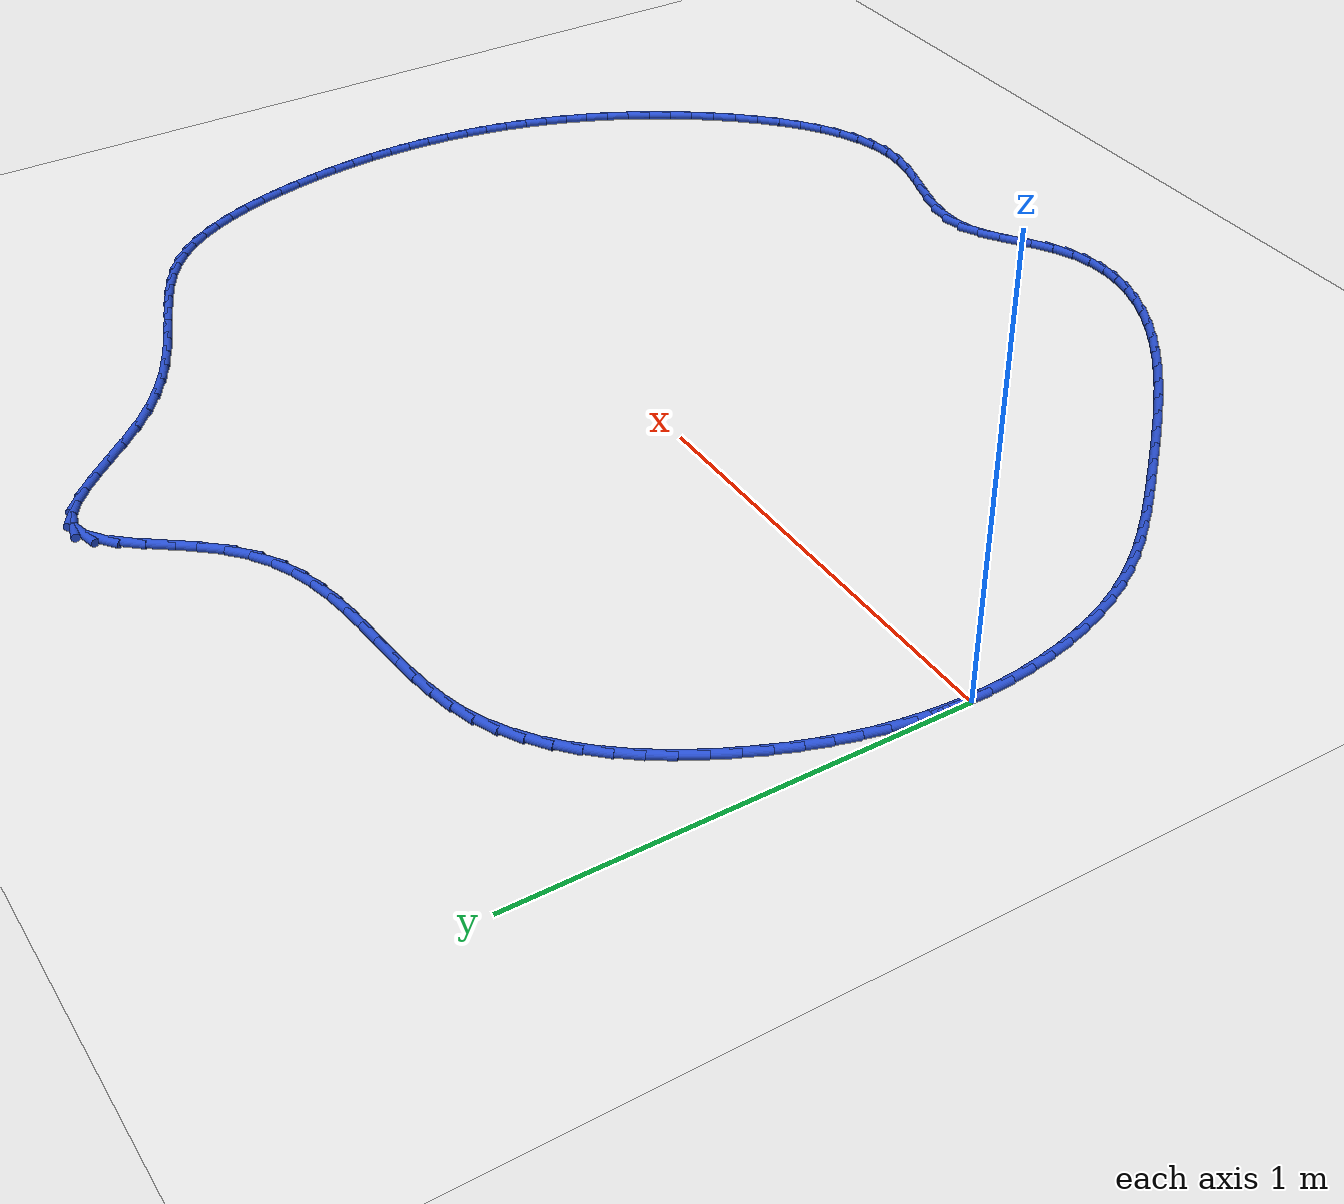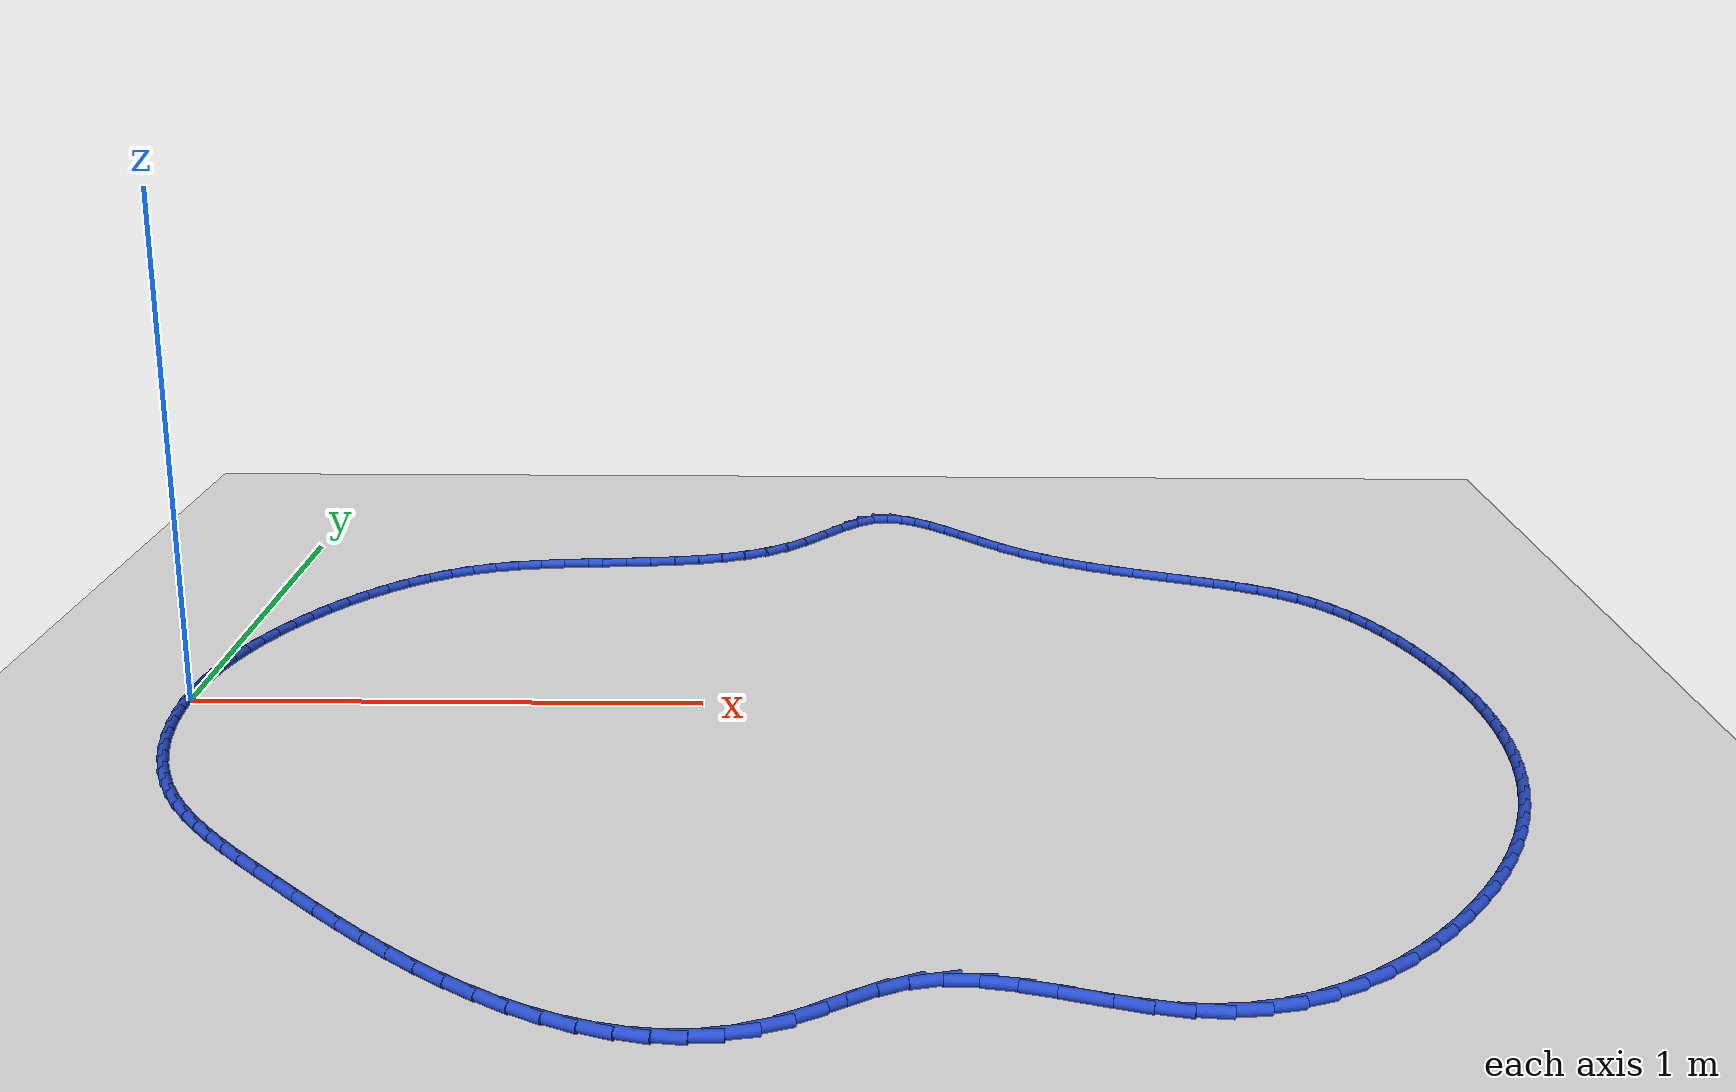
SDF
<sdf version="1.6">
 <world name="default">
  <light name="sun" type="directional">
   <pose>0 0 10 0 -0 0</pose>
   <diffuse>0.8 0.8 0.8 1</diffuse>
   <specular>0.2 0.2 0.2 1</specular>
   <attenuation>
    <range>1000</range>
    <constant>0.9</constant>
    <linear>0.01</linear>
    <quadratic>0.001</quadratic>
   </attenuation>
   <direction>-0.5 0.1 -0.9</direction>
  </light>
  <model name="ground_plane">
   <static>1</static>
   <link name="link">
    <collision name="collision">
     <geometry><plane><normal>0 0 1</normal><size>100 100</size></plane></geometry>
     <surface><friction><ode><mu>100</mu><mu2>50</mu2></ode></friction></surface>
    </collision>
    <visual name="visual">
     <cast_shadows>0</cast_shadows>
     <geometry><plane><normal>0 0 1</normal><size>100 100</size></plane></geometry>
     <material>
      <script><uri>file://media/materials/scripts/gazebo.material</uri><name>Gazebo/WhiteGlow</name></script>
     </material>
    </visual>
   </link>
  </model>
  <gravity>0 0 -9.8</gravity>
  <magnetic_field>6e-06 2.3e-05 -4.2e-05</magnetic_field>
  <atmosphere type="adiabatic"/>
  <physics name="default_physics" default="0" type="ode">
   <max_step_size>0.001</max_step_size>
   <real_time_factor>1</real_time_factor>
   <real_time_update_rate>1000</real_time_update_rate>
  </physics>
  <scene><ambient>0.4 0.4 0.4 1</ambient><background>0.7 0.7 0.7 1</background><shadows>1</shadows></scene>
  <spherical_coordinates>
   <surface_model>EARTH_WGS84</surface_model>
   <latitude_deg>0</latitude_deg>
   <longitude_deg>0</longitude_deg>
   <elevation>0</elevation>
   <heading_deg>0</heading_deg>
  </spherical_coordinates>
  <model name="line">
   <link name="link_0">
    <pose>2.42861286636753e-17 1.3877787807814457e-17 0.01 0 1.57 1.5420624588516978</pose>
    <collision name="collision">
     <geometry><cylinder><radius>0.01</radius><length>0.08</length></cylinder></geometry>
    </collision>
    <visual name="visual">
     <material>
      <script><name>Gazebo/Blue</name><uri>file://media/materials/scripts/gazebo.material</uri></script>
     </material>
     <geometry><cylinder><radius>0.01</radius><length>0.08</length></cylinder></geometry>
    </visual>
   </link>
   <link name="link_1">
    <pose>0.0015752846020971303 0.054808181222139235 0.01 0 1.57 1.4864380276648332</pose>
    <collision name="collision">
     <geometry><cylinder><radius>0.01</radius><length>0.08</length></cylinder></geometry>
    </collision>
    <visual name="visual">
     <material>
      <script><name>Gazebo/Blue</name><uri>file://media/materials/scripts/gazebo.material</uri></script>
     </material>
     <geometry><cylinder><radius>0.01</radius><length>0.08</length></cylinder></geometry>
    </visual>
   </link>
   <link name="link_2">
    <pose>0.006167575423817304 0.10911691302079636 0.01 0 1.57 1.43100222677461</pose>
    <collision name="collision">
     <geometry><cylinder><radius>0.01</radius><length>0.08</length></cylinder></geometry>
    </collision>
    <visual name="visual">
     <material>
      <script><name>Gazebo/Blue</name><uri>file://media/materials/scripts/gazebo.material</uri></script>
     </material>
     <geometry><cylinder><radius>0.01</radius><length>0.08</length></cylinder></geometry>
    </visual>
   </link>
   <link name="link_3">
    <pose>0.01374115883125542 0.16294024106731586 0.01 0 1.57 1.3761278261949221</pose>
    <collision name="collision">
     <geometry><cylinder><radius>0.01</radius><length>0.08</length></cylinder></geometry>
    </collision>
    <visual name="visual">
     <material>
      <script><name>Gazebo/Blue</name><uri>file://media/materials/scripts/gazebo.material</uri></script>
     </material>
     <geometry><cylinder><radius>0.01</radius><length>0.08</length></cylinder></geometry>
    </visual>
   </link>
   <link name="link_4">
    <pose>0.024260321190506334 0.21629221103304203 0.01 0 1.57 1.3221669012426487</pose>
    <collision name="collision">
     <geometry><cylinder><radius>0.01</radius><length>0.08</length></cylinder></geometry>
    </collision>
    <visual name="visual">
     <material>
      <script><name>Gazebo/Blue</name><uri>file://media/materials/scripts/gazebo.material</uri></script>
     </material>
     <geometry><cylinder><radius>0.01</radius><length>0.08</length></cylinder></geometry>
    </visual>
   </link>
   <link name="link_5">
    <pose>0.03768934886766492 0.26918686858931923 0.01 0 1.57 1.2694385844756824</pose>
    <collision name="collision">
     <geometry><cylinder><radius>0.01</radius><length>0.08</length></cylinder></geometry>
    </collision>
    <visual name="visual">
     <material>
      <script><name>Gazebo/Blue</name><uri>file://media/materials/scripts/gazebo.material</uri></script>
     </material>
     <geometry><cylinder><radius>0.01</radius><length>0.08</length></cylinder></geometry>
    </visual>
   </link>
   <link name="link_6">
    <pose>0.05399252822882604 0.32163825940749213 0.01 0 1.57 1.2182197417365341</pose>
    <collision name="collision">
     <geometry><cylinder><radius>0.01</radius><length>0.08</length></cylinder></geometry>
    </collision>
    <visual name="visual">
     <material>
      <script><name>Gazebo/Blue</name><uri>file://media/materials/scripts/gazebo.material</uri></script>
     </material>
     <geometry><cylinder><radius>0.01</radius><length>0.08</length></cylinder></geometry>
    </visual>
   </link>
   <link name="link_7">
    <pose>0.07313414564008455 0.3736604291589047 0.01 0 1.57 1.1687390947016263</pose>
    <collision name="collision">
     <geometry><cylinder><radius>0.01</radius><length>0.08</length></cylinder></geometry>
    </collision>
    <visual name="visual">
     <material>
      <script><name>Gazebo/Blue</name><uri>file://media/materials/scripts/gazebo.material</uri></script>
     </material>
     <geometry><cylinder><radius>0.01</radius><length>0.08</length></cylinder></geometry>
    </visual>
   </link>
   <link name="link_8">
    <pose>0.09507848746753535 0.42526742351490165 0.01 0 1.57 1.1206531839875287</pose>
    <collision name="collision">
     <geometry><cylinder><radius>0.01</radius><length>0.08</length></cylinder></geometry>
    </collision>
    <visual name="visual">
     <material>
      <script><name>Gazebo/Blue</name><uri>file://media/materials/scripts/gazebo.material</uri></script>
     </material>
     <geometry><cylinder><radius>0.01</radius><length>0.08</length></cylinder></geometry>
    </visual>
   </link>
   <link name="link_9">
    <pose>0.11979248727167095 0.4764105993432065 0.01 0 1.57 1.0702290029019654</pose>
    <collision name="collision">
     <geometry><cylinder><radius>0.01</radius><length>0.08</length></cylinder></geometry>
    </collision>
    <visual name="visual">
     <material>
      <script><name>Gazebo/Blue</name><uri>file://media/materials/scripts/gazebo.material</uri></script>
     </material>
     <geometry><cylinder><radius>0.01</radius><length>0.08</length></cylinder></geometry>
    </visual>
   </link>
   <link name="link_10">
    <pose>0.14726073606709572 0.5266231633846747 0.01 0 1.57 1.0149843644139154</pose>
    <collision name="collision">
     <geometry><cylinder><radius>0.01</radius><length>0.08</length></cylinder></geometry>
    </collision>
    <visual name="visual">
     <material>
      <script><name>Gazebo/Blue</name><uri>file://media/materials/scripts/gazebo.material</uri></script>
     </material>
     <geometry><cylinder><radius>0.01</radius><length>0.08</length></cylinder></geometry>
    </visual>
   </link>
   <link name="link_11">
    <pose>0.17747504987871773 0.5752672252924358 0.01 0 1.57 0.953650546992467</pose>
    <collision name="collision">
     <geometry><cylinder><radius>0.01</radius><length>0.08</length></cylinder></geometry>
    </collision>
    <visual name="visual">
     <material>
      <script><name>Gazebo/Blue</name><uri>file://media/materials/scripts/gazebo.material</uri></script>
     </material>
     <geometry><cylinder><radius>0.01</radius><length>0.08</length></cylinder></geometry>
    </visual>
   </link>
   <link name="link_12">
    <pose>0.21042726639922063 0.6217043816001717 0.01 0 1.57 0.884848366604672</pose>
    <collision name="collision">
     <geometry><cylinder><radius>0.01</radius><length>0.08</length></cylinder></geometry>
    </collision>
    <visual name="visual">
     <material>
      <script><name>Gazebo/Blue</name><uri>file://media/materials/scripts/gazebo.material</uri></script>
     </material>
     <geometry><cylinder><radius>0.01</radius><length>0.08</length></cylinder></geometry>
    </visual>
   </link>
   <link name="link_13">
    <pose>0.2461092233212879 0.6652962288415646 0.01 0 1.57 0.8071061710454825</pose>
    <collision name="collision">
     <geometry><cylinder><radius>0.01</radius><length>0.08</length></cylinder></geometry>
    </collision>
    <visual name="visual">
     <material>
      <script><name>Gazebo/Blue</name><uri>file://media/materials/scripts/gazebo.material</uri></script>
     </material>
     <geometry><cylinder><radius>0.01</radius><length>0.08</length></cylinder></geometry>
    </visual>
   </link>
   <link name="link_14">
    <pose>0.2845127583376033 0.7054043635502972 0.01 0 1.57 0.7189496441462482</pose>
    <collision name="collision">
     <geometry><cylinder><radius>0.01</radius><length>0.08</length></cylinder></geometry>
    </collision>
    <visual name="visual">
     <material>
      <script><name>Gazebo/Blue</name><uri>file://media/materials/scripts/gazebo.material</uri></script>
     </material>
     <geometry><cylinder><radius>0.01</radius><length>0.08</length></cylinder></geometry>
    </visual>
   </link>
   <link name="link_15">
    <pose>0.3256297091408505 0.7413903822600517 0.01 0 1.57 0.6190990299214362</pose>
    <collision name="collision">
     <geometry><cylinder><radius>0.01</radius><length>0.08</length></cylinder></geometry>
    </collision>
    <visual name="visual">
     <material>
      <script><name>Gazebo/Blue</name><uri>file://media/materials/scripts/gazebo.material</uri></script>
     </material>
     <geometry><cylinder><radius>0.01</radius><length>0.08</length></cylinder></geometry>
    </visual>
   </link>
   <link name="link_16">
    <pose>0.36945191342371314 0.7726158815045103 0.01 0 1.57 0.5068113766488609</pose>
    <collision name="collision">
     <geometry><cylinder><radius>0.01</radius><length>0.08</length></cylinder></geometry>
    </collision>
    <visual name="visual">
     <material>
      <script><name>Gazebo/Blue</name><uri>file://media/materials/scripts/gazebo.material</uri></script>
     </material>
     <geometry><cylinder><radius>0.01</radius><length>0.08</length></cylinder></geometry>
    </visual>
   </link>
   <link name="link_17">
    <pose>0.41597120887887473 0.7984424578173552 0.01 0 1.57 0.3843534324642805</pose>
    <collision name="collision">
     <geometry><cylinder><radius>0.01</radius><length>0.08</length></cylinder></geometry>
    </collision>
    <visual name="visual">
     <material>
      <script><name>Gazebo/Blue</name><uri>file://media/materials/scripts/gazebo.material</uri></script>
     </material>
     <geometry><cylinder><radius>0.01</radius><length>0.08</length></cylinder></geometry>
    </visual>
   </link>
   <link name="link_18">
    <pose>0.4651529781041939 0.8183349826380478 0.01 0 1.57 0.27401545991121457</pose>
    <collision name="collision">
     <geometry><cylinder><radius>0.01</radius><length>0.08</length></cylinder></geometry>
    </collision>
    <visual name="visual">
     <material>
      <script><name>Gazebo/Blue</name><uri>file://media/materials/scripts/gazebo.material</uri></script>
     </material>
     <geometry><cylinder><radius>0.01</radius><length>0.08</length></cylinder></geometry>
    </visual>
   </link>
   <link name="link_19">
    <pose>0.5166902855572811 0.8328213978830915 0.01 0 1.57 0.18926324430584604</pose>
    <collision name="collision">
     <geometry><cylinder><radius>0.01</radius><length>0.08</length></cylinder></geometry>
    </collision>
    <visual name="visual">
     <material>
      <script><name>Gazebo/Blue</name><uri>file://media/materials/scripts/gazebo.material</uri></script>
     </material>
     <geometry><cylinder><radius>0.01</radius><length>0.08</length></cylinder></geometry>
    </visual>
   </link>
   <link name="link_20">
    <pose>0.5701159032129353 0.8430553922738603 0.01 0 1.57 0.1295169135766608</pose>
    <collision name="collision">
     <geometry><cylinder><radius>0.01</radius><length>0.08</length></cylinder></geometry>
    </collision>
    <visual name="visual">
     <material>
      <script><name>Gazebo/Blue</name><uri>file://media/materials/scripts/gazebo.material</uri></script>
     </material>
     <geometry><cylinder><radius>0.01</radius><length>0.08</length></cylinder></geometry>
    </visual>
   </link>
   <link name="link_21">
    <pose>0.624960545223401 0.850198687821038 0.01 0 1.57 0.0931853184821633</pose>
    <collision name="collision">
     <geometry><cylinder><radius>0.01</radius><length>0.08</length></cylinder></geometry>
    </collision>
    <visual name="visual">
     <material>
      <script><name>Gazebo/Blue</name><uri>file://media/materials/scripts/gazebo.material</uri></script>
     </material>
     <geometry><cylinder><radius>0.01</radius><length>0.08</length></cylinder></geometry>
    </visual>
   </link>
   <link name="link_22">
    <pose>0.6807549257409228 0.8554130065353077 0.01 0 1.57 0.07886014349723709</pose>
    <collision name="collision">
     <geometry><cylinder><radius>0.01</radius><length>0.08</length></cylinder></geometry>
    </collision>
    <visual name="visual">
     <material>
      <script><name>Gazebo/Blue</name><uri>file://media/materials/scripts/gazebo.material</uri></script>
     </material>
     <geometry><cylinder><radius>0.01</radius><length>0.08</length></cylinder></geometry>
    </visual>
   </link>
   <link name="link_23">
    <pose>0.7370297589177452 0.8598600704273529 0.01 0 1.57 0.08580540829288871</pose>
    <collision name="collision">
     <geometry><cylinder><radius>0.01</radius><length>0.08</length></cylinder></geometry>
    </collision>
    <visual name="visual">
     <material>
      <script><name>Gazebo/Blue</name><uri>file://media/materials/scripts/gazebo.material</uri></script>
     </material>
     <geometry><cylinder><radius>0.01</radius><length>0.08</length></cylinder></geometry>
    </visual>
   </link>
   <link name="link_24">
    <pose>0.7933157589061129 0.8647016015078569 0.01 0 1.57 0.11409949158228143</pose>
    <collision name="collision">
     <geometry><cylinder><radius>0.01</radius><length>0.08</length></cylinder></geometry>
    </collision>
    <visual name="visual">
     <material>
      <script><name>Gazebo/Blue</name><uri>file://media/materials/scripts/gazebo.material</uri></script>
     </material>
     <geometry><cylinder><radius>0.01</radius><length>0.08</length></cylinder></geometry>
    </visual>
   </link>
   <link name="link_25">
    <pose>0.8491436398582705 0.8710993217875033 0.01 0 1.57 0.16453811369930088</pose>
    <collision name="collision">
     <geometry><cylinder><radius>0.01</radius><length>0.08</length></cylinder></geometry>
    </collision>
    <visual name="visual">
     <material>
      <script><name>Gazebo/Blue</name><uri>file://media/materials/scripts/gazebo.material</uri></script>
     </material>
     <geometry><cylinder><radius>0.01</radius><length>0.08</length></cylinder></geometry>
    </visual>
   </link>
   <link name="link_26">
    <pose>0.904044115926462 0.880214953276975 0.01 0 1.57 0.23827102497982827</pose>
    <collision name="collision">
     <geometry><cylinder><radius>0.01</radius><length>0.08</length></cylinder></geometry>
    </collision>
    <visual name="visual">
     <material>
      <script><name>Gazebo/Blue</name><uri>file://media/materials/scripts/gazebo.material</uri></script>
     </material>
     <geometry><cylinder><radius>0.01</radius><length>0.08</length></cylinder></geometry>
    </visual>
   </link>
   <link name="link_27">
    <pose>0.9575479012629324 0.8932102179869557 0.01 0 1.57 0.33604302087828597</pose>
    <collision name="collision">
     <geometry><cylinder><radius>0.01</radius><length>0.08</length></cylinder></geometry>
    </collision>
    <visual name="visual">
     <material>
      <script><name>Gazebo/Blue</name><uri>file://media/materials/scripts/gazebo.material</uri></script>
     </material>
     <geometry><cylinder><radius>0.01</radius><length>0.08</length></cylinder></geometry>
    </visual>
   </link>
   <link name="link_28">
    <pose>1.0091857100199264 0.9112468379281284 0.01 0 1.57 0.4569469614177471</pose>
    <collision name="collision">
     <geometry><cylinder><radius>0.01</radius><length>0.08</length></cylinder></geometry>
    </collision>
    <visual name="visual">
     <material>
      <script><name>Gazebo/Blue</name><uri>file://media/materials/scripts/gazebo.material</uri></script>
     </material>
     <geometry><cylinder><radius>0.01</radius><length>0.08</length></cylinder></geometry>
    </visual>
   </link>
   <link name="link_29">
    <pose>1.0584882563496882 0.9354865351111767 0.01 0 1.57 0.5969686504758093</pose>
    <collision name="collision">
     <geometry><cylinder><radius>0.01</radius><length>0.08</length></cylinder></geometry>
    </collision>
    <visual name="visual">
     <material>
      <script><name>Gazebo/Blue</name><uri>file://media/materials/scripts/gazebo.material</uri></script>
     </material>
     <geometry><cylinder><radius>0.01</radius><length>0.08</length></cylinder></geometry>
    </visual>
   </link>
   <link name="link_30">
    <pose>1.1049862544044626 0.9670910315467844 0.01 0 1.57 0.7478115857028584</pose>
    <collision name="collision">
     <geometry><cylinder><radius>0.01</radius><length>0.08</length></cylinder></geometry>
    </collision>
    <visual name="visual">
     <material>
      <script><name>Gazebo/Blue</name><uri>file://media/materials/scripts/gazebo.material</uri></script>
     </material>
     <geometry><cylinder><radius>0.01</radius><length>0.08</length></cylinder></geometry>
    </visual>
   </link>
   <link name="link_31">
    <pose>1.14821746689511 1.007188720057224 0.01 0 1.57 0.870567117872888</pose>
    <collision name="collision">
     <geometry><cylinder><radius>0.01</radius><length>0.08</length></cylinder></geometry>
    </collision>
    <visual name="visual">
     <material>
      <script><name>Gazebo/Blue</name><uri>file://media/materials/scripts/gazebo.material</uri></script>
     </material>
     <geometry><cylinder><radius>0.01</radius><length>0.08</length></cylinder></geometry>
    </visual>
   </link>
   <link name="link_32">
    <pose>1.1882001866343026 1.0546358014928792 0.01 0 1.57 0.9265381492743721</pose>
    <collision name="collision">
     <geometry><cylinder><radius>0.01</radius><length>0.08</length></cylinder></geometry>
    </collision>
    <visual name="visual">
     <material>
      <script><name>Gazebo/Blue</name><uri>file://media/materials/scripts/gazebo.material</uri></script>
     </material>
     <geometry><cylinder><radius>0.01</radius><length>0.08</length></cylinder></geometry>
    </visual>
   </link>
   <link name="link_33">
    <pose>1.2257326943667566 1.1046002950258593 0.01 0 1.57 0.9209991003880702</pose>
    <collision name="collision">
     <geometry><cylinder><radius>0.01</radius><length>0.08</length></cylinder></geometry>
    </collision>
    <visual name="visual">
     <material>
      <script><name>Gazebo/Blue</name><uri>file://media/materials/scripts/gazebo.material</uri></script>
     </material>
     <geometry><cylinder><radius>0.01</radius><length>0.08</length></cylinder></geometry>
    </visual>
   </link>
   <link name="link_34">
    <pose>1.261684651981534 1.1519126932872454 0.01 0 1.57 0.8422033054999151</pose>
    <collision name="collision">
     <geometry><cylinder><radius>0.01</radius><length>0.08</length></cylinder></geometry>
    </collision>
    <visual name="visual">
     <material>
      <script><name>Gazebo/Blue</name><uri>file://media/materials/scripts/gazebo.material</uri></script>
     </material>
     <geometry><cylinder><radius>0.01</radius><length>0.08</length></cylinder></geometry>
    </visual>
   </link>
   <link name="link_35">
    <pose>1.2969257213676955 1.1914034889081215 0.01 0 1.57 0.6425929764301397</pose>
    <collision name="collision">
     <geometry><cylinder><radius>0.01</radius><length>0.08</length></cylinder></geometry>
    </collision>
    <visual name="visual">
     <material>
      <script><name>Gazebo/Blue</name><uri>file://media/materials/scripts/gazebo.material</uri></script>
     </material>
     <geometry><cylinder><radius>0.01</radius><length>0.08</length></cylinder></geometry>
    </visual>
   </link>
   <link name="link_36">
    <pose>1.3323255644143026 1.2179031745195692 0.01 0 1.57 0.23117182751288756</pose>
    <collision name="collision">
     <geometry><cylinder><radius>0.01</radius><length>0.08</length></cylinder></geometry>
    </collision>
    <visual name="visual">
     <material>
      <script><name>Gazebo/Blue</name><uri>file://media/materials/scripts/gazebo.material</uri></script>
     </material>
     <geometry><cylinder><radius>0.01</radius><length>0.08</length></cylinder></geometry>
    </visual>
   </link>
   <link name="link_37">
    <pose>1.3687316749913365 1.226472436559535 0.01 0 1.57 -0.2560467390787924</pose>
    <collision name="collision">
     <geometry><cylinder><radius>0.01</radius><length>0.08</length></cylinder></geometry>
    </collision>
    <visual name="visual">
     <material>
      <script><name>Gazebo/Blue</name><uri>file://media/materials/scripts/gazebo.material</uri></script>
     </material>
     <geometry><cylinder><radius>0.01</radius><length>0.08</length></cylinder></geometry>
    </visual>
   </link>
   <link name="link_38">
    <pose>1.4065682904966756 1.216567077612201 0.01 0 1.57 -0.5660232831014738</pose>
    <collision name="collision">
     <geometry><cylinder><radius>0.01</radius><length>0.08</length></cylinder></geometry>
    </collision>
    <visual name="visual">
     <material>
      <script><name>Gazebo/Blue</name><uri>file://media/materials/scripts/gazebo.material</uri></script>
     </material>
     <geometry><cylinder><radius>0.01</radius><length>0.08</length></cylinder></geometry>
    </visual>
   </link>
   <link name="link_39">
    <pose>1.4458795568515859 1.1915897889593532 0.01 0 1.57 -0.7297121862824675</pose>
    <collision name="collision">
     <geometry><cylinder><radius>0.01</radius><length>0.08</length></cylinder></geometry>
    </collision>
    <visual name="visual">
     <material>
      <script><name>Gazebo/Blue</name><uri>file://media/materials/scripts/gazebo.material</uri></script>
     </material>
     <geometry><cylinder><radius>0.01</radius><length>0.08</length></cylinder></geometry>
    </visual>
   </link>
   <link name="link_40">
    <pose>1.4866961162823493 1.1550834849195244 0.01 0 1.57 -0.8100337775588168</pose>
    <collision name="collision">
     <geometry><cylinder><radius>0.01</radius><length>0.08</length></cylinder></geometry>
    </collision>
    <visual name="visual">
     <material>
      <script><name>Gazebo/Blue</name><uri>file://media/materials/scripts/gazebo.material</uri></script>
     </material>
     <geometry><cylinder><radius>0.01</radius><length>0.08</length></cylinder></geometry>
    </visual>
   </link>
   <link name="link_41">
    <pose>1.5290486110152515 1.1105910798112473 0.01 0 1.57 -0.8393711922237244</pose>
    <collision name="collision">
     <geometry><cylinder><radius>0.01</radius><length>0.08</length></cylinder></geometry>
    </collision>
    <visual name="visual">
     <material>
      <script><name>Gazebo/Blue</name><uri>file://media/materials/scripts/gazebo.material</uri></script>
     </material>
     <geometry><cylinder><radius>0.01</radius><length>0.08</length></cylinder></geometry>
    </visual>
   </link>
   <link name="link_42">
    <pose>1.5729676832765767 1.0616554879530562 0.01 0 1.57 -0.8306684665896843</pose>
    <collision name="collision">
     <geometry><cylinder><radius>0.01</radius><length>0.08</length></cylinder></geometry>
    </collision>
    <visual name="visual">
     <material>
      <script><name>Gazebo/Blue</name><uri>file://media/materials/scripts/gazebo.material</uri></script>
     </material>
     <geometry><cylinder><radius>0.01</radius><length>0.08</length></cylinder></geometry>
    </visual>
   </link>
   <link name="link_43">
    <pose>1.6184839752926072 1.0118196236634833 0.01 0 1.57 -0.7859183008323506</pose>
    <collision name="collision">
     <geometry><cylinder><radius>0.01</radius><length>0.08</length></cylinder></geometry>
    </collision>
    <visual name="visual">
     <material>
      <script><name>Gazebo/Blue</name><uri>file://media/materials/scripts/gazebo.material</uri></script>
     </material>
     <geometry><cylinder><radius>0.01</radius><length>0.08</length></cylinder></geometry>
    </visual>
   </link>
   <link name="link_44">
    <pose>1.6656281292896287 0.964626401261061 0.01 0 1.57 -0.7053604683465347</pose>
    <collision name="collision">
     <geometry><cylinder><radius>0.01</radius><length>0.08</length></cylinder></geometry>
    </collision>
    <visual name="visual">
     <material>
      <script><name>Gazebo/Blue</name><uri>file://media/materials/scripts/gazebo.material</uri></script>
     </material>
     <geometry><cylinder><radius>0.01</radius><length>0.08</length></cylinder></geometry>
    </visual>
   </link>
   <link name="link_45">
    <pose>1.714380977160737 0.9231136691036133 0.01 0 1.57 -0.6196559004188579</pose>
    <collision name="collision">
     <geometry><cylinder><radius>0.01</radius><length>0.08</length></cylinder></geometry>
    </collision>
    <visual name="visual">
     <material>
      <script><name>Gazebo/Blue</name><uri>file://media/materials/scripts/gazebo.material</uri></script>
     </material>
     <geometry><cylinder><radius>0.01</radius><length>0.08</length></cylinder></geometry>
    </visual>
   </link>
   <link name="link_46">
    <pose>1.7644359385053168 0.8874049773108945 0.01 0 1.57 -0.5440994701484362</pose>
    <collision name="collision">
     <geometry><cylinder><radius>0.01</radius><length>0.08</length></cylinder></geometry>
    </collision>
    <visual name="visual">
     <material>
      <script><name>Gazebo/Blue</name><uri>file://media/materials/scripts/gazebo.material</uri></script>
     </material>
     <geometry><cylinder><radius>0.01</radius><length>0.08</length></cylinder></geometry>
    </visual>
   </link>
   <link name="link_47">
    <pose>1.815383568519732 0.8565808532961623 0.01 0 1.57 -0.4812987626477115</pose>
    <collision name="collision">
     <geometry><cylinder><radius>0.01</radius><length>0.08</length></cylinder></geometry>
    </collision>
    <visual name="visual">
     <material>
      <script><name>Gazebo/Blue</name><uri>file://media/materials/scripts/gazebo.material</uri></script>
     </material>
     <geometry><cylinder><radius>0.01</radius><length>0.08</length></cylinder></geometry>
    </visual>
   </link>
   <link name="link_48">
    <pose>1.8668142920668012 0.8297205029187824 0.01 0 1.57 -0.4331467290565228</pose>
    <collision name="collision">
     <geometry><cylinder><radius>0.01</radius><length>0.08</length></cylinder></geometry>
    </collision>
    <visual name="visual">
     <material>
      <script><name>Gazebo/Blue</name><uri>file://media/materials/scripts/gazebo.material</uri></script>
     </material>
     <geometry><cylinder><radius>0.01</radius><length>0.08</length></cylinder></geometry>
    </visual>
   </link>
   <link name="link_49">
    <pose>1.9183185340093396 0.8059031320381218 0.01 0 1.57 -0.40102126294946877</pose>
    <collision name="collision">
     <geometry><cylinder><radius>0.01</radius><length>0.08</length></cylinder></geometry>
    </collision>
    <visual name="visual">
     <material>
      <script><name>Gazebo/Blue</name><uri>file://media/materials/scripts/gazebo.material</uri></script>
     </material>
     <geometry><cylinder><radius>0.01</radius><length>0.08</length></cylinder></geometry>
    </visual>
   </link>
   <link name="link_50">
    <pose>1.9694867192101648 0.7842079465135462 0.01 0 1.57 -0.3860466238513498</pose>
    <collision name="collision">
     <geometry><cylinder><radius>0.01</radius><length>0.08</length></cylinder></geometry>
    </collision>
    <visual name="visual">
     <material>
      <script><name>Gazebo/Blue</name><uri>file://media/materials/scripts/gazebo.material</uri></script>
     </material>
     <geometry><cylinder><radius>0.01</radius><length>0.08</length></cylinder></geometry>
    </visual>
   </link>
   <link name="link_51">
    <pose>2.0199092725320926 0.7637141522044222 0.01 0 1.57 -0.38933327146834834</pose>
    <collision name="collision">
     <geometry><cylinder><radius>0.01</radius><length>0.08</length></cylinder></geometry>
    </collision>
    <visual name="visual">
     <material>
      <script><name>Gazebo/Blue</name><uri>file://media/materials/scripts/gazebo.material</uri></script>
     </material>
     <geometry><cylinder><radius>0.01</radius><length>0.08</length></cylinder></geometry>
    </visual>
   </link>
   <link name="link_52">
    <pose>2.0691766188379397 0.7435009549701156 0.01 0 1.57 -0.4121204768248951</pose>
    <collision name="collision">
     <geometry><cylinder><radius>0.01</radius><length>0.08</length></cylinder></geometry>
    </collision>
    <visual name="visual">
     <material>
      <script><name>Gazebo/Blue</name><uri>file://media/materials/scripts/gazebo.material</uri></script>
     </material>
     <geometry><cylinder><radius>0.01</radius><length>0.08</length></cylinder></geometry>
    </visual>
   </link>
   <link name="link_53">
    <pose>2.1168791829905222 0.7226475606699929 0.01 0 1.57 -0.45574903315459</pose>
    <collision name="collision">
     <geometry><cylinder><radius>0.01</radius><length>0.08</length></cylinder></geometry>
    </collision>
    <visual name="visual">
     <material>
      <script><name>Gazebo/Blue</name><uri>file://media/materials/scripts/gazebo.material</uri></script>
     </material>
     <geometry><cylinder><radius>0.01</radius><length>0.08</length></cylinder></geometry>
    </visual>
   </link>
   <link name="link_54">
    <pose>2.1626073898526577 0.7002331751634202 0.01 0 1.57 -0.5213697091800215</pose>
    <collision name="collision">
     <geometry><cylinder><radius>0.01</radius><length>0.08</length></cylinder></geometry>
    </collision>
    <visual name="visual">
     <material>
      <script><name>Gazebo/Blue</name><uri>file://media/materials/scripts/gazebo.material</uri></script>
     </material>
     <geometry><cylinder><radius>0.01</radius><length>0.08</length></cylinder></geometry>
    </visual>
   </link>
   <link name="link_55">
    <pose>2.205951664287162 0.6753370043097637 0.01 0 1.57 -0.6092881485719072</pose>
    <collision name="collision">
     <geometry><cylinder><radius>0.01</radius><length>0.08</length></cylinder></geometry>
    </collision>
    <visual name="visual">
     <material>
      <script><name>Gazebo/Blue</name><uri>file://media/materials/scripts/gazebo.material</uri></script>
     </material>
     <geometry><cylinder><radius>0.01</radius><length>0.08</length></cylinder></geometry>
    </visual>
   </link>
   <link name="link_56">
    <pose>2.246502431156852 0.6470382539683901 0.01 0 1.57 -0.7179634357631732</pose>
    <collision name="collision">
     <geometry><cylinder><radius>0.01</radius><length>0.08</length></cylinder></geometry>
    </collision>
    <visual name="visual">
     <material>
      <script><name>Gazebo/Blue</name><uri>file://media/materials/scripts/gazebo.material</uri></script>
     </material>
     <geometry><cylinder><radius>0.01</radius><length>0.08</length></cylinder></geometry>
    </visual>
   </link>
   <link name="link_57">
    <pose>2.283850115324544 0.6144161299986648 0.01 0 1.57 -0.8401181218053861</pose>
    <collision name="collision">
     <geometry><cylinder><radius>0.01</radius><length>0.08</length></cylinder></geometry>
    </collision>
    <visual name="visual">
     <material>
      <script><name>Gazebo/Blue</name><uri>file://media/materials/scripts/gazebo.material</uri></script>
     </material>
     <geometry><cylinder><radius>0.01</radius><length>0.08</length></cylinder></geometry>
    </visual>
   </link>
   <link name="link_58">
    <pose>2.3176432618474703 0.5767064414686103 0.01 0 1.57 -0.9518142964372253</pose>
    <collision name="collision">
     <geometry><cylinder><radius>0.01</radius><length>0.08</length></cylinder></geometry>
    </collision>
    <visual name="visual">
     <material>
      <script><name>Gazebo/Blue</name><uri>file://media/materials/scripts/gazebo.material</uri></script>
     </material>
     <geometry><cylinder><radius>0.01</radius><length>0.08</length></cylinder></geometry>
    </visual>
   </link>
   <link name="link_59">
    <pose>2.3479225612927976 0.5342016223548923 0.01 0 1.57 -1.0458993241131336</pose>
    <collision name="collision">
     <geometry><cylinder><radius>0.01</radius><length>0.08</length></cylinder></geometry>
    </collision>
    <visual name="visual">
     <material>
      <script><name>Gazebo/Blue</name><uri>file://media/materials/scripts/gazebo.material</uri></script>
     </material>
     <geometry><cylinder><radius>0.01</radius><length>0.08</length></cylinder></geometry>
    </visual>
   </link>
   <link name="link_60">
    <pose>2.3748908278472105 0.4876309441098679 0.01 0 1.57 -1.1248125704359455</pose>
    <collision name="collision">
     <geometry><cylinder><radius>0.01</radius><length>0.08</length></cylinder></geometry>
    </collision>
    <visual name="visual">
     <material>
      <script><name>Gazebo/Blue</name><uri>file://media/materials/scripts/gazebo.material</uri></script>
     </material>
     <geometry><cylinder><radius>0.01</radius><length>0.08</length></cylinder></geometry>
    </visual>
   </link>
   <link name="link_61">
    <pose>2.3987513897697648 0.4377250633392593 0.01 0 1.57 -1.1910779744897673</pose>
    <collision name="collision">
     <geometry><cylinder><radius>0.01</radius><length>0.08</length></cylinder></geometry>
    </collision>
    <visual name="visual">
     <material>
      <script><name>Gazebo/Blue</name><uri>file://media/materials/scripts/gazebo.material</uri></script>
     </material>
     <geometry><cylinder><radius>0.01</radius><length>0.08</length></cylinder></geometry>
    </visual>
   </link>
   <link name="link_62">
    <pose>2.419707575319518 0.38521463664878963 0.01 0 1.57 -1.246945007474544</pose>
    <collision name="collision">
     <geometry><cylinder><radius>0.01</radius><length>0.08</length></cylinder></geometry>
    </collision>
    <visual name="visual">
     <material>
      <script><name>Gazebo/Blue</name><uri>file://media/materials/scripts/gazebo.material</uri></script>
     </material>
     <geometry><cylinder><radius>0.01</radius><length>0.08</length></cylinder></geometry>
    </visual>
   </link>
   <link name="link_63">
    <pose>2.4379627127555246 0.33083032064418055 0.01 0 1.57 -1.2942890518727148</pose>
    <collision name="collision">
     <geometry><cylinder><radius>0.01</radius><length>0.08</length></cylinder></geometry>
    </collision>
    <visual name="visual">
     <material>
      <script><name>Gazebo/Blue</name><uri>file://media/materials/scripts/gazebo.material</uri></script>
     </material>
     <geometry><cylinder><radius>0.01</radius><length>0.08</length></cylinder></geometry>
    </visual>
   </link>
   <link name="link_64">
    <pose>2.4537201303368428 0.2753027719311555 0.01 0 1.57 -1.3347752834350097</pose>
    <collision name="collision">
     <geometry><cylinder><radius>0.01</radius><length>0.08</length></cylinder></geometry>
    </collision>
    <visual name="visual">
     <material>
      <script><name>Gazebo/Blue</name><uri>file://media/materials/scripts/gazebo.material</uri></script>
     </material>
     <geometry><cylinder><radius>0.01</radius><length>0.08</length></cylinder></geometry>
    </visual>
   </link>
   <link name="link_65">
    <pose>2.46717788145442 0.21934621079997654 0.01 0 1.57 -1.3726238532755404</pose>
    <collision name="collision">
     <geometry><cylinder><radius>0.01</radius><length>0.08</length></cylinder></geometry>
    </collision>
    <visual name="visual">
     <material>
      <script><name>Gazebo/Blue</name><uri>file://media/materials/scripts/gazebo.material</uri></script>
     </material>
     <geometry><cylinder><radius>0.01</radius><length>0.08</length></cylinder></geometry>
    </visual>
   </link>
   <link name="link_66">
    <pose>2.478425218837699 0.16333583825956866 0.01 0 1.57 -1.4110499724930692</pose>
    <collision name="collision">
     <geometry><cylinder><radius>0.01</radius><length>0.08</length></cylinder></geometry>
    </collision>
    <visual name="visual">
     <material>
      <script><name>Gazebo/Blue</name><uri>file://media/materials/scripts/gazebo.material</uri></script>
     </material>
     <geometry><cylinder><radius>0.01</radius><length>0.08</length></cylinder></geometry>
    </visual>
   </link>
   <link name="link_67">
    <pose>2.4874491271899997 0.10732819151445805 0.01 0 1.57 -1.450166023117443</pose>
    <collision name="collision">
     <geometry><cylinder><radius>0.01</radius><length>0.08</length></cylinder></geometry>
    </collision>
    <visual name="visual">
     <material>
      <script><name>Gazebo/Blue</name><uri>file://media/materials/scripts/gazebo.material</uri></script>
     </material>
     <geometry><cylinder><radius>0.01</radius><length>0.08</length></cylinder></geometry>
    </visual>
   </link>
   <link name="link_68">
    <pose>2.494232624444166 0.05136744744287516 0.01 0 1.57 -1.4899610210386731</pose>
    <collision name="collision">
     <geometry><cylinder><radius>0.01</radius><length>0.08</length></cylinder></geometry>
    </collision>
    <visual name="visual">
     <material>
      <script><name>Gazebo/Blue</name><uri>file://media/materials/scripts/gazebo.material</uri></script>
     </material>
     <geometry><cylinder><radius>0.01</radius><length>0.08</length></cylinder></geometry>
    </visual>
   </link>
   <link name="link_69">
    <pose>2.498758728533042 -0.004502217076947528 0.01 0 1.57 -1.5304172323101213</pose>
    <collision name="collision">
     <geometry><cylinder><radius>0.01</radius><length>0.08</length></cylinder></geometry>
    </collision>
    <visual name="visual">
     <material>
      <script><name>Gazebo/Blue</name><uri>file://media/materials/scripts/gazebo.material</uri></script>
     </material>
     <geometry><cylinder><radius>0.01</radius><length>0.08</length></cylinder></geometry>
    </visual>
   </link>
   <link name="link_70">
    <pose>2.5010104573894694 -0.06023662516677945 0.01 0 1.57 1.5700830074817</pose>
    <collision name="collision">
     <geometry><cylinder><radius>0.01</radius><length>0.08</length></cylinder></geometry>
    </collision>
    <visual name="visual">
     <material>
      <script><name>Gazebo/Blue</name><uri>file://media/materials/scripts/gazebo.material</uri></script>
     </material>
     <geometry><cylinder><radius>0.01</radius><length>0.08</length></cylinder></geometry>
    </visual>
   </link>
   <link name="link_71">
    <pose>2.500970828946292 -0.11579159994838845 0.01 0 1.57 1.5283871070189952</pose>
    <collision name="collision">
     <geometry><cylinder><radius>0.01</radius><length>0.08</length></cylinder></geometry>
    </collision>
    <visual name="visual">
     <material>
      <script><name>Gazebo/Blue</name><uri>file://media/materials/scripts/gazebo.material</uri></script>
     </material>
     <geometry><cylinder><radius>0.01</radius><length>0.08</length></cylinder></geometry>
    </visual>
   </link>
   <link name="link_72">
    <pose>2.4986228611363543 -0.17112296454354337 0.01 0 1.57 1.486128438291383</pose>
    <collision name="collision">
     <geometry><cylinder><radius>0.01</radius><length>0.08</length></cylinder></geometry>
    </collision>
    <visual name="visual">
     <material>
      <script><name>Gazebo/Blue</name><uri>file://media/materials/scripts/gazebo.material</uri></script>
     </material>
     <geometry><cylinder><radius>0.01</radius><length>0.08</length></cylinder></geometry>
    </visual>
   </link>
   <link name="link_73">
    <pose>2.493949571892497 -0.22618654207401365 0.01 0 1.57 1.4433558579246348</pose>
    <collision name="collision">
     <geometry><cylinder><radius>0.01</radius><length>0.08</length></cylinder></geometry>
    </collision>
    <visual name="visual">
     <material>
      <script><name>Gazebo/Blue</name><uri>file://media/materials/scripts/gazebo.material</uri></script>
     </material>
     <geometry><cylinder><radius>0.01</radius><length>0.08</length></cylinder></geometry>
    </visual>
   </link>
   <link name="link_74">
    <pose>2.4869339791475653 -0.28093815566156627 0.01 0 1.57 1.4001263064421006</pose>
    <collision name="collision">
     <geometry><cylinder><radius>0.01</radius><length>0.08</length></cylinder></geometry>
    </collision>
    <visual name="visual">
     <material>
      <script><name>Gazebo/Blue</name><uri>file://media/materials/scripts/gazebo.material</uri></script>
     </material>
     <geometry><cylinder><radius>0.01</radius><length>0.08</length></cylinder></geometry>
    </visual>
   </link>
   <link name="link_75">
    <pose>2.477559100834401 -0.33533362842797043 0.01 0 1.57 1.3565045412479382</pose>
    <collision name="collision">
     <geometry><cylinder><radius>0.01</radius><length>0.08</length></cylinder></geometry>
    </collision>
    <visual name="visual">
     <material>
      <script><name>Gazebo/Blue</name><uri>file://media/materials/scripts/gazebo.material</uri></script>
     </material>
     <geometry><cylinder><radius>0.01</radius><length>0.08</length></cylinder></geometry>
    </visual>
   </link>
   <link name="link_76">
    <pose>2.465807954885849 -0.3893287834949949 0.01 0 1.57 1.3125626423972914</pose>
    <collision name="collision">
     <geometry><cylinder><radius>0.01</radius><length>0.08</length></cylinder></geometry>
    </collision>
    <visual name="visual">
     <material>
      <script><name>Gazebo/Blue</name><uri>file://media/materials/scripts/gazebo.material</uri></script>
     </material>
     <geometry><cylinder><radius>0.01</radius><length>0.08</length></cylinder></geometry>
    </visual>
   </link>
   <link name="link_77">
    <pose>2.451663559234751 -0.4428794439844081 0.01 0 1.57 1.268379287133359</pose>
    <collision name="collision">
     <geometry><cylinder><radius>0.01</radius><length>0.08</length></cylinder></geometry>
    </collision>
    <visual name="visual">
     <material>
      <script><name>Gazebo/Blue</name><uri>file://media/materials/scripts/gazebo.material</uri></script>
     </material>
     <geometry><cylinder><radius>0.01</radius><length>0.08</length></cylinder></geometry>
    </visual>
   </link>
   <link name="link_78">
    <pose>2.435108931813949 -0.4959414330179793 0.01 0 1.57 1.2240388014329284</pose>
    <collision name="collision">
     <geometry><cylinder><radius>0.01</radius><length>0.08</length></cylinder></geometry>
    </collision>
    <visual name="visual">
     <material>
      <script><name>Gazebo/Blue</name><uri>file://media/materials/scripts/gazebo.material</uri></script>
     </material>
     <geometry><cylinder><radius>0.01</radius><length>0.08</length></cylinder></geometry>
    </visual>
   </link>
   <link name="link_79">
    <pose>2.416127090556289 -0.5484705737174757 0.01 0 1.57 1.179630009917066</pose>
    <collision name="collision">
     <geometry><cylinder><radius>0.01</radius><length>0.08</length></cylinder></geometry>
    </collision>
    <visual name="visual">
     <material>
      <script><name>Gazebo/Blue</name><uri>file://media/materials/scripts/gazebo.material</uri></script>
     </material>
     <geometry><cylinder><radius>0.01</radius><length>0.08</length></cylinder></geometry>
    </visual>
   </link>
   <link name="link_80">
    <pose>2.394701053394612 -0.6004226892046665 0.01 0 1.57 1.1352449183064932</pose>
    <collision name="collision">
     <geometry><cylinder><radius>0.01</radius><length>0.08</length></cylinder></geometry>
    </collision>
    <visual name="visual">
     <material>
      <script><name>Gazebo/Blue</name><uri>file://media/materials/scripts/gazebo.material</uri></script>
     </material>
     <geometry><cylinder><radius>0.01</radius><length>0.08</length></cylinder></geometry>
    </visual>
   </link>
   <link name="link_81">
    <pose>2.3708138382617623 -0.6517536026013202 0.01 0 1.57 1.0909772738800108</pose>
    <collision name="collision">
     <geometry><cylinder><radius>0.01</radius><length>0.08</length></cylinder></geometry>
    </collision>
    <visual name="visual">
     <material>
      <script><name>Gazebo/Blue</name><uri>file://media/materials/scripts/gazebo.material</uri></script>
     </material>
     <geometry><cylinder><radius>0.01</radius><length>0.08</length></cylinder></geometry>
    </visual>
   </link>
   <link name="link_82">
    <pose>2.3444484630905826 -0.7024191370292063 0.01 0 1.57 1.0469210579464674</pose>
    <collision name="collision">
     <geometry><cylinder><radius>0.01</radius><length>0.08</length></cylinder></geometry>
    </collision>
    <visual name="visual">
     <material>
      <script><name>Gazebo/Blue</name><uri>file://media/materials/scripts/gazebo.material</uri></script>
     </material>
     <geometry><cylinder><radius>0.01</radius><length>0.08</length></cylinder></geometry>
    </visual>
   </link>
   <link name="link_83">
    <pose>2.315587945813916 -0.7523751156100917 0.01 0 1.57 1.0031689692139265</pose>
    <collision name="collision">
     <geometry><cylinder><radius>0.01</radius><length>0.08</length></cylinder></geometry>
    </collision>
    <visual name="visual">
     <material>
      <script><name>Gazebo/Blue</name><uri>file://media/materials/scripts/gazebo.material</uri></script>
     </material>
     <geometry><cylinder><radius>0.01</radius><length>0.08</length></cylinder></geometry>
    </visual>
   </link>
   <link name="link_84">
    <pose>2.284215304364607 -0.801577361465746 0.01 0 1.57 0.9598109575816097</pose>
    <collision name="collision">
     <geometry><cylinder><radius>0.01</radius><length>0.08</length></cylinder></geometry>
    </collision>
    <visual name="visual">
     <material>
      <script><name>Gazebo/Blue</name><uri>file://media/materials/scripts/gazebo.material</uri></script>
     </material>
     <geometry><cylinder><radius>0.01</radius><length>0.08</length></cylinder></geometry>
    </visual>
   </link>
   <link name="link_85">
    <pose>2.2503135566754966 -0.8499816977179372 0.01 0 1.57 0.9166849161648355</pose>
    <collision name="collision">
     <geometry><cylinder><radius>0.01</radius><length>0.08</length></cylinder></geometry>
    </collision>
    <visual name="visual">
     <material>
      <script><name>Gazebo/Blue</name><uri>file://media/materials/scripts/gazebo.material</uri></script>
     </material>
     <geometry><cylinder><radius>0.01</radius><length>0.08</length></cylinder></geometry>
    </visual>
   </link>
   <link name="link_86">
    <pose>2.213872777022656 -0.8975103257216526 0.01 0 1.57 0.8701835564440691</pose>
    <collision name="collision">
     <geometry><cylinder><radius>0.01</radius><length>0.08</length></cylinder></geometry>
    </collision>
    <visual name="visual">
     <material>
      <script><name>Gazebo/Blue</name><uri>file://media/materials/scripts/gazebo.material</uri></script>
     </material>
     <geometry><cylinder><radius>0.01</radius><length>0.08</length></cylinder></geometry>
    </visual>
   </link>
   <link name="link_87">
    <pose>2.1749787091725885 -0.9436296048763467 0.01 0 1.57 0.8166123963825668</pose>
    <collision name="collision">
     <geometry><cylinder><radius>0.01</radius><length>0.08</length></cylinder></geometry>
    </collision>
    <visual name="visual">
     <material>
      <script><name>Gazebo/Blue</name><uri>file://media/materials/scripts/gazebo.material</uri></script>
     </material>
     <geometry><cylinder><radius>0.01</radius><length>0.08</length></cylinder></geometry>
    </visual>
   </link>
   <link name="link_88">
    <pose>2.133785980885139 -0.9874776790334768 0.01 0 1.57 0.7541450641752144</pose>
    <collision name="collision">
     <geometry><cylinder><radius>0.01</radius><length>0.08</length></cylinder></geometry>
    </collision>
    <visual name="visual">
     <material>
      <script><name>Gazebo/Blue</name><uri>file://media/materials/scripts/gazebo.material</uri></script>
     </material>
     <geometry><cylinder><radius>0.01</radius><length>0.08</length></cylinder></geometry>
    </visual>
   </link>
   <link name="link_89">
    <pose>2.090450737312075 -1.0281854620394106 0.01 0 1.57 0.6806475786405304</pose>
    <collision name="collision">
     <geometry><cylinder><radius>0.01</radius><length>0.08</length></cylinder></geometry>
    </collision>
    <visual name="visual">
     <material>
      <script><name>Gazebo/Blue</name><uri>file://media/materials/scripts/gazebo.material</uri></script>
     </material>
     <geometry><cylinder><radius>0.01</radius><length>0.08</length></cylinder></geometry>
    </visual>
   </link>
   <link name="link_90">
    <pose>2.045129123605168 -1.0648838677405152 0.01 0 1.57 0.5936396734217847</pose>
    <collision name="collision">
     <geometry><cylinder><radius>0.01</radius><length>0.08</length></cylinder></geometry>
    </collision>
    <visual name="visual">
     <material>
      <script><name>Gazebo/Blue</name><uri>file://media/materials/scripts/gazebo.material</uri></script>
     </material>
     <geometry><cylinder><radius>0.01</radius><length>0.08</length></cylinder></geometry>
    </visual>
   </link>
   <link name="link_91">
    <pose>1.9979772849161874 -1.0967038099831583 0.01 0 1.57 0.49046588903584254</pose>
    <collision name="collision">
     <geometry><cylinder><radius>0.01</radius><length>0.08</length></cylinder></geometry>
    </collision>
    <visual name="visual">
     <material>
      <script><name>Gazebo/Blue</name><uri>file://media/materials/scripts/gazebo.material</uri></script>
     </material>
     <geometry><cylinder><radius>0.01</radius><length>0.08</length></cylinder></geometry>
    </visual>
   </link>
   <link name="link_92">
    <pose>1.9491513663969036 -1.1227762026137056 0.01 0 1.57 0.3687775239050474</pose>
    <collision name="collision">
     <geometry><cylinder><radius>0.01</radius><length>0.08</length></cylinder></geometry>
    </collision>
    <visual name="visual">
     <material>
      <script><name>Gazebo/Blue</name><uri>file://media/materials/scripts/gazebo.material</uri></script>
     </material>
     <geometry><cylinder><radius>0.01</radius><length>0.08</length></cylinder></geometry>
    </visual>
   </link>
   <link name="link_93">
    <pose>1.8988075131990865 -1.1422319594785248 0.01 0 1.57 0.22749583656582623</pose>
    <collision name="collision">
     <geometry><cylinder><radius>0.01</radius><length>0.08</length></cylinder></geometry>
    </collision>
    <visual name="visual">
     <material>
      <script><name>Gazebo/Blue</name><uri>file://media/materials/scripts/gazebo.material</uri></script>
     </material>
     <geometry><cylinder><radius>0.01</radius><length>0.08</length></cylinder></geometry>
    </visual>
   </link>
   <link name="link_94">
    <pose>1.8471018704745048 -1.154201994423983 0.01 0 1.57 0.0682201647040794</pose>
    <collision name="collision">
     <geometry><cylinder><radius>0.01</radius><length>0.08</length></cylinder></geometry>
    </collision>
    <visual name="visual">
     <material>
      <script><name>Gazebo/Blue</name><uri>file://media/materials/scripts/gazebo.material</uri></script>
     </material>
     <geometry><cylinder><radius>0.01</radius><length>0.08</length></cylinder></geometry>
    </visual>
   </link>
   <link name="link_95">
    <pose>1.7941905833749288 -1.1578172212964473 0.01 0 1.57 -0.10131250406398866</pose>
    <collision name="collision">
     <geometry><cylinder><radius>0.01</radius><length>0.08</length></cylinder></geometry>
    </collision>
    <visual name="visual">
     <material>
      <script><name>Gazebo/Blue</name><uri>file://media/materials/scripts/gazebo.material</uri></script>
     </material>
     <geometry><cylinder><radius>0.01</radius><length>0.08</length></cylinder></geometry>
    </visual>
   </link>
   <link name="link_96">
    <pose>1.7402385353224916 -1.1523324256324585 0.01 0 1.57 -0.23543015963167893</pose>
    <collision name="collision">
     <geometry><cylinder><radius>0.01</radius><length>0.08</length></cylinder></geometry>
    </collision>
    <visual name="visual">
     <material>
      <script><name>Gazebo/Blue</name><uri>file://media/materials/scripts/gazebo.material</uri></script>
     </material>
     <geometry><cylinder><radius>0.01</radius><length>0.08</length></cylinder></geometry>
    </visual>
   </link>
   <link name="link_97">
    <pose>1.6855668960263022 -1.1392178710571594 0.01 0 1.57 -0.3061132833511059</pose>
    <collision name="collision">
     <geometry><cylinder><radius>0.01</radius><length>0.08</length></cylinder></geometry>
    </collision>
    <visual name="visual">
     <material>
      <script><name>Gazebo/Blue</name><uri>file://media/materials/scripts/gazebo.material</uri></script>
     </material>
     <geometry><cylinder><radius>0.01</radius><length>0.08</length></cylinder></geometry>
    </visual>
   </link>
   <link name="link_98">
    <pose>1.6306317085424689 -1.1218557544227732 0.01 0 1.57 -0.3204123119250425</pose>
    <collision name="collision">
     <geometry><cylinder><radius>0.01</radius><length>0.08</length></cylinder></geometry>
    </collision>
    <visual name="visual">
     <material>
      <script><name>Gazebo/Blue</name><uri>file://media/materials/scripts/gazebo.material</uri></script>
     </material>
     <geometry><cylinder><radius>0.01</radius><length>0.08</length></cylinder></geometry>
    </visual>
   </link>
   <link name="link_99">
    <pose>1.5758934424387085 -1.1036910217815101 0.01 0 1.57 -0.2795082879275666</pose>
    <collision name="collision">
     <geometry><cylinder><radius>0.01</radius><length>0.08</length></cylinder></geometry>
    </collision>
    <visual name="visual">
     <material>
      <script><name>Gazebo/Blue</name><uri>file://media/materials/scripts/gazebo.material</uri></script>
     </material>
     <geometry><cylinder><radius>0.01</radius><length>0.08</length></cylinder></geometry>
    </visual>
   </link>
   <link name="link_100">
    <pose>1.5218125672827365 -1.0881686191855802 0.01 0 1.57 -0.1762961283496022</pose>
    <collision name="collision">
     <geometry><cylinder><radius>0.01</radius><length>0.08</length></cylinder></geometry>
    </collision>
    <visual name="visual">
     <material>
      <script><name>Gazebo/Blue</name><uri>file://media/materials/scripts/gazebo.material</uri></script>
     </material>
     <geometry><cylinder><radius>0.01</radius><length>0.08</length></cylinder></geometry>
    </visual>
   </link>
   <link name="link_101">
    <pose>1.4688495526422716 -1.078733492687194 0.01 0 1.57 0.0018895812369772143</pose>
    <collision name="collision">
     <geometry><cylinder><radius>0.01</radius><length>0.08</length></cylinder></geometry>
    </collision>
    <visual name="visual">
     <material>
      <script><name>Gazebo/Blue</name><uri>file://media/materials/scripts/gazebo.material</uri></script>
     </material>
     <geometry><cylinder><radius>0.01</radius><length>0.08</length></cylinder></geometry>
    </visual>
   </link>
   <link name="link_102">
    <pose>1.4174648680850295 -1.078830588338562 0.01 0 1.57 0.2561401413071853</pose>
    <collision name="collision">
     <geometry><cylinder><radius>0.01</radius><length>0.08</length></cylinder></geometry>
    </collision>
    <visual name="visual">
     <material>
      <script><name>Gazebo/Blue</name><uri>file://media/materials/scripts/gazebo.material</uri></script>
     </material>
     <geometry><cylinder><radius>0.01</radius><length>0.08</length></cylinder></geometry>
    </visual>
   </link>
   <link name="link_103">
    <pose>1.3680990908685853 -1.091759127469802 0.01 0 1.57 0.4836374194559097</pose>
    <collision name="collision">
     <geometry><cylinder><radius>0.01</radius><length>0.08</length></cylinder></geometry>
    </collision>
    <visual name="visual">
     <material>
      <script><name>Gazebo/Blue</name><uri>file://media/materials/scripts/gazebo.material</uri></script>
     </material>
     <geometry><cylinder><radius>0.01</radius><length>0.08</length></cylinder></geometry>
    </visual>
   </link>
   <link name="link_104">
    <pose>1.320629551747051 -1.1166921670989662 0.01 0 1.57 0.5971894880573649</pose>
    <collision name="collision">
     <geometry><cylinder><radius>0.01</radius><length>0.08</length></cylinder></geometry>
    </collision>
    <visual name="visual">
     <material>
      <script><name>Gazebo/Blue</name><uri>file://media/materials/scripts/gazebo.material</uri></script>
     </material>
     <geometry><cylinder><radius>0.01</radius><length>0.08</length></cylinder></geometry>
    </visual>
   </link>
   <link name="link_105">
    <pose>1.2743044697149488 -1.1481940920646 0.01 0 1.57 0.6138834764074463</pose>
    <collision name="collision">
     <geometry><cylinder><radius>0.01</radius><length>0.08</length></cylinder></geometry>
    </collision>
    <visual name="visual">
     <material>
      <script><name>Gazebo/Blue</name><uri>file://media/materials/scripts/gazebo.material</uri></script>
     </material>
     <geometry><cylinder><radius>0.01</radius><length>0.08</length></cylinder></geometry>
    </visual>
   </link>
   <link name="link_106">
    <pose>1.2283389478792905 -1.1805866907712537 0.01 0 1.57 0.5368214430394034</pose>
    <collision name="collision">
     <geometry><cylinder><radius>0.01</radius><length>0.08</length></cylinder></geometry>
    </collision>
    <visual name="visual">
     <material>
      <script><name>Gazebo/Blue</name><uri>file://media/materials/scripts/gazebo.material</uri></script>
     </material>
     <geometry><cylinder><radius>0.01</radius><length>0.08</length></cylinder></geometry>
    </visual>
   </link>
   <link name="link_107">
    <pose>1.181948491728032 -1.2081944473952826 0.01 0 1.57 0.3758071325182721</pose>
    <collision name="collision">
     <geometry><cylinder><radius>0.01</radius><length>0.08</length></cylinder></geometry>
    </collision>
    <visual name="visual">
     <material>
      <script><name>Gazebo/Blue</name><uri>file://media/materials/scripts/gazebo.material</uri></script>
     </material>
     <geometry><cylinder><radius>0.01</radius><length>0.08</length></cylinder></geometry>
    </visual>
   </link>
   <link name="link_108">
    <pose>1.1345788776668382 -1.2268845579593644 0.01 0 1.57 0.19946547344628981</pose>
    <collision name="collision">
     <geometry><cylinder><radius>0.01</radius><length>0.08</length></cylinder></geometry>
    </collision>
    <visual name="visual">
     <material>
      <script><name>Gazebo/Blue</name><uri>file://media/materials/scripts/gazebo.material</uri></script>
     </material>
     <geometry><cylinder><radius>0.01</radius><length>0.08</length></cylinder></geometry>
    </visual>
   </link>
   <link name="link_109">
    <pose>1.0862911295388369 -1.2366461003097218 0.01 0 1.57 0.03063872361794845</pose>
    <collision name="collision">
     <geometry><cylinder><radius>0.01</radius><length>0.08</length></cylinder></geometry>
    </collision>
    <visual name="visual">
     <material>
      <script><name>Gazebo/Blue</name><uri>file://media/materials/scripts/gazebo.material</uri></script>
     </material>
     <geometry><cylinder><radius>0.01</radius><length>0.08</length></cylinder></geometry>
    </visual>
   </link>
   <link name="link_110">
    <pose>1.0372479256873433 -1.2381491918403682 0.01 0 1.57 -0.12198865534891509</pose>
    <collision name="collision">
     <geometry><cylinder><radius>0.01</radius><length>0.08</length></cylinder></geometry>
    </collision>
    <visual name="visual">
     <material>
      <script><name>Gazebo/Blue</name><uri>file://media/materials/scripts/gazebo.material</uri></script>
     </material>
     <geometry><cylinder><radius>0.01</radius><length>0.08</length></cylinder></geometry>
    </visual>
   </link>
   <link name="link_111">
    <pose>0.9876119444556687 -1.2320639499453174 0.01 0 1.57 -0.2541113004921439</pose>
    <collision name="collision">
     <geometry><cylinder><radius>0.01</radius><length>0.08</length></cylinder></geometry>
    </collision>
    <visual name="visual">
     <material>
      <script><name>Gazebo/Blue</name><uri>file://media/materials/scripts/gazebo.material</uri></script>
     </material>
     <geometry><cylinder><radius>0.01</radius><length>0.08</length></cylinder></geometry>
    </visual>
   </link>
   <link name="link_112">
    <pose>0.9375458641871273 -1.2190604920185837 0.01 0 1.57 -0.36531228260544407</pose>
    <collision name="collision">
     <geometry><cylinder><radius>0.01</radius><length>0.08</length></cylinder></geometry>
    </collision>
    <visual name="visual">
     <material>
      <script><name>Gazebo/Blue</name><uri>file://media/materials/scripts/gazebo.material</uri></script>
     </material>
     <geometry><cylinder><radius>0.01</radius><length>0.08</length></cylinder></geometry>
    </visual>
   </link>
   <link name="link_113">
    <pose>0.8872123632250308 -1.1998089354541805 0.01 0 1.57 -0.4574493561994801</pose>
    <collision name="collision">
     <geometry><cylinder><radius>0.01</radius><length>0.08</length></cylinder></geometry>
    </collision>
    <visual name="visual">
     <material>
      <script><name>Gazebo/Blue</name><uri>file://media/materials/scripts/gazebo.material</uri></script>
     </material>
     <geometry><cylinder><radius>0.01</radius><length>0.08</length></cylinder></geometry>
    </visual>
   </link>
   <link name="link_114">
    <pose>0.8367741199126939 -1.1749793976461214 0.01 0 1.57 -0.5332257961167922</pose>
    <collision name="collision">
     <geometry><cylinder><radius>0.01</radius><length>0.08</length></cylinder></geometry>
    </collision>
    <visual name="visual">
     <material>
      <script><name>Gazebo/Blue</name><uri>file://media/materials/scripts/gazebo.material</uri></script>
     </material>
     <geometry><cylinder><radius>0.01</radius><length>0.08</length></cylinder></geometry>
    </visual>
   </link>
   <link name="link_115">
    <pose>0.7863938125934291 -1.145241995988421 0.01 0 1.57 -0.5953552292238156</pose>
    <collision name="collision">
     <geometry><cylinder><radius>0.01</radius><length>0.08</length></cylinder></geometry>
    </collision>
    <visual name="visual">
     <material>
      <script><name>Gazebo/Blue</name><uri>file://media/materials/scripts/gazebo.material</uri></script>
     </material>
     <geometry><cylinder><radius>0.01</radius><length>0.08</length></cylinder></geometry>
    </visual>
   </link>
   <link name="link_116">
    <pose>0.7362341196105496 -1.111266847875092 0.01 0 1.57 -0.6462018277554729</pose>
    <collision name="collision">
     <geometry><cylinder><radius>0.01</radius><length>0.08</length></cylinder></geometry>
    </collision>
    <visual name="visual">
     <material>
      <script><name>Gazebo/Blue</name><uri>file://media/materials/scripts/gazebo.material</uri></script>
     </material>
     <geometry><cylinder><radius>0.01</radius><length>0.08</length></cylinder></geometry>
    </visual>
   </link>
   <link name="link_117">
    <pose>0.6864577193073675 -1.0737240707001483 0.01 0 1.57 -0.6876834774751353</pose>
    <collision name="collision">
     <geometry><cylinder><radius>0.01</radius><length>0.08</length></cylinder></geometry>
    </collision>
    <visual name="visual">
     <material>
      <script><name>Gazebo/Blue</name><uri>file://media/materials/scripts/gazebo.material</uri></script>
     </material>
     <geometry><cylinder><radius>0.01</radius><length>0.08</length></cylinder></geometry>
    </visual>
   </link>
   <link name="link_118">
    <pose>0.6372272900271974 -1.0332837818576042 0.01 0 1.57 -0.7212890619989076</pose>
    <collision name="collision">
     <geometry><cylinder><radius>0.01</radius><length>0.08</length></cylinder></geometry>
    </collision>
    <visual name="visual">
     <material>
      <script><name>Gazebo/Blue</name><uri>file://media/materials/scripts/gazebo.material</uri></script>
     </material>
     <geometry><cylinder><radius>0.01</radius><length>0.08</length></cylinder></geometry>
    </visual>
   </link>
   <link name="link_119">
    <pose>0.5887055101133516 -0.9906160987414737 0.01 0 1.57 -0.7481313236049429</pose>
    <collision name="collision">
     <geometry><cylinder><radius>0.01</radius><length>0.08</length></cylinder></geometry>
    </collision>
    <visual name="visual">
     <material>
      <script><name>Gazebo/Blue</name><uri>file://media/materials/scripts/gazebo.material</uri></script>
     </material>
     <geometry><cylinder><radius>0.01</radius><length>0.08</length></cylinder></geometry>
    </visual>
   </link>
   <link name="link_120">
    <pose>0.5410550579091434 -0.9463911387457697 0.01 0 1.57 -0.7689998711382078</pose>
    <collision name="collision">
     <geometry><cylinder><radius>0.01</radius><length>0.08</length></cylinder></geometry>
    </collision>
    <visual name="visual">
     <material>
      <script><name>Gazebo/Blue</name><uri>file://media/materials/scripts/gazebo.material</uri></script>
     </material>
     <geometry><cylinder><radius>0.01</radius><length>0.08</length></cylinder></geometry>
    </visual>
   </link>
   <link name="link_121">
    <pose>0.49443861175788584 -0.9012790192645066 0.01 0 1.57 -0.784399802769446</pose>
    <collision name="collision">
     <geometry><cylinder><radius>0.01</radius><length>0.08</length></cylinder></geometry>
    </collision>
    <visual name="visual">
     <material>
      <script><name>Gazebo/Blue</name><uri>file://media/materials/scripts/gazebo.material</uri></script>
     </material>
     <geometry><cylinder><radius>0.01</radius><length>0.08</length></cylinder></geometry>
    </visual>
   </link>
   <link name="link_122">
    <pose>0.4490188500028911 -0.8559498576916971 0.01 0 1.57 -0.7945694768601932</pose>
    <collision name="collision">
     <geometry><cylinder><radius>0.01</radius><length>0.08</length></cylinder></geometry>
    </collision>
    <visual name="visual">
     <material>
      <script><name>Gazebo/Blue</name><uri>file://media/materials/scripts/gazebo.material</uri></script>
     </material>
     <geometry><cylinder><radius>0.01</radius><length>0.08</length></cylinder></geometry>
    </visual>
   </link>
   <link name="link_123">
    <pose>0.4049584509874741 -0.8110737714213565 0.01 0 1.57 -0.7995545535776921</pose>
    <collision name="collision">
     <geometry><cylinder><radius>0.01</radius><length>0.08</length></cylinder></geometry>
    </collision>
    <visual name="visual">
     <material>
      <script><name>Gazebo/Blue</name><uri>file://media/materials/scripts/gazebo.material</uri></script>
     </material>
     <geometry><cylinder><radius>0.01</radius><length>0.08</length></cylinder></geometry>
    </visual>
   </link>
   <link name="link_124">
    <pose>0.3624200027643242 -0.7673135641429227 0.01 0 1.57 -0.8040630930343449</pose>
    <collision name="collision">
     <geometry><cylinder><radius>0.01</radius><length>0.08</length></cylinder></geometry>
    </collision>
    <visual name="visual">
     <material>
      <script><name>Gazebo/Blue</name><uri>file://media/materials/scripts/gazebo.material</uri></script>
     </material>
     <geometry><cylinder><radius>0.01</radius><length>0.08</length></cylinder></geometry>
    </visual>
   </link>
   <link name="link_125">
    <pose>0.32156075789327293 -0.7248998549243851 0.01 0 1.57 -0.8160797458655416</pose>
    <collision name="collision">
     <geometry><cylinder><radius>0.01</radius><length>0.08</length></cylinder></geometry>
    </collision>
    <visual name="visual">
     <material>
      <script><name>Gazebo/Blue</name><uri>file://media/materials/scripts/gazebo.material</uri></script>
     </material>
     <geometry><cylinder><radius>0.01</radius><length>0.08</length></cylinder></geometry>
    </visual>
   </link>
   <link name="link_126">
    <pose>0.282529745697302 -0.6833971656992374 0.01 0 1.57 -0.836921920277842</pose>
    <collision name="collision">
     <geometry><cylinder><radius>0.01</radius><length>0.08</length></cylinder></geometry>
    </collision>
    <visual name="visual">
     <material>
      <script><name>Gazebo/Blue</name><uri>file://media/materials/scripts/gazebo.material</uri></script>
     </material>
     <geometry><cylinder><radius>0.01</radius><length>0.08</length></cylinder></geometry>
    </visual>
   </link>
   <link name="link_127">
    <pose>0.24547529356324171 -0.6423131602964541 0.01 0 1.57 -0.8670707324574061</pose>
    <collision name="collision">
     <geometry><cylinder><radius>0.01</radius><length>0.08</length></cylinder></geometry>
    </collision>
    <visual name="visual">
     <material>
      <script><name>Gazebo/Blue</name><uri>file://media/materials/scripts/gazebo.material</uri></script>
     </material>
     <geometry><cylinder><radius>0.01</radius><length>0.08</length></cylinder></geometry>
    </visual>
   </link>
   <link name="link_128">
    <pose>0.21054572887792056 -0.6011555025450088 0.01 0 1.57 -0.9067046611781485</pose>
    <collision name="collision">
     <geometry><cylinder><radius>0.01</radius><length>0.08</length></cylinder></geometry>
    </collision>
    <visual name="visual">
     <material>
      <script><name>Gazebo/Blue</name><uri>file://media/materials/scripts/gazebo.material</uri></script>
     </material>
     <geometry><cylinder><radius>0.01</radius><length>0.08</length></cylinder></geometry>
    </visual>
   </link>
   <link name="link_129">
    <pose>0.17788937902816765 -0.5594318562738748 0.01 0 1.57 -0.9555755619991757</pose>
    <collision name="collision">
     <geometry><cylinder><radius>0.01</radius><length>0.08</length></cylinder></geometry>
    </collision>
    <visual name="visual">
     <material>
      <script><name>Gazebo/Blue</name><uri>file://media/materials/scripts/gazebo.material</uri></script>
     </material>
     <geometry><cylinder><radius>0.01</radius><length>0.08</length></cylinder></geometry>
    </visual>
   </link>
   <link name="link_130">
    <pose>0.14765457140081206 -0.5166498853120255 0.01 0 1.57 -1.0128941004056617</pose>
    <collision name="collision">
     <geometry><cylinder><radius>0.01</radius><length>0.08</length></cylinder></geometry>
    </collision>
    <visual name="visual">
     <material>
      <script><name>Gazebo/Blue</name><uri>file://media/materials/scripts/gazebo.material</uri></script>
     </material>
     <geometry><cylinder><radius>0.01</radius><length>0.08</length></cylinder></geometry>
    </visual>
   </link>
   <link name="link_131">
    <pose>0.11998963338268252 -0.47231725348843395 0.01 0 1.57 -1.077261138981261</pose>
    <collision name="collision">
     <geometry><cylinder><radius>0.01</radius><length>0.08</length></cylinder></geometry>
    </collision>
    <visual name="visual">
     <material>
      <script><name>Gazebo/Blue</name><uri>file://media/materials/scripts/gazebo.material</uri></script>
     </material>
     <geometry><cylinder><radius>0.01</radius><length>0.08</length></cylinder></geometry>
    </visual>
   </link>
   <link name="link_132">
    <pose>0.09504279603218801 -0.4259422974435999 0.01 0 1.57 -1.1444537857581092</pose>
    <collision name="collision">
     <geometry><cylinder><radius>0.01</radius><length>0.08</length></cylinder></geometry>
    </collision>
    <visual name="visual">
     <material>
      <script><name>Gazebo/Blue</name><uri>file://media/materials/scripts/gazebo.material</uri></script>
     </material>
     <geometry><cylinder><radius>0.01</radius><length>0.08</length></cylinder></geometry>
    </visual>
   </link>
   <link name="link_133">
    <pose>0.07293017018231704 -0.3772576994224191 0.01 0 1.57 -1.2081704735092884</pose>
    <collision name="collision">
     <geometry><cylinder><radius>0.01</radius><length>0.08</length></cylinder></geometry>
    </collision>
    <visual name="visual">
     <material>
      <script><name>Gazebo/Blue</name><uri>file://media/materials/scripts/gazebo.material</uri></script>
     </material>
     <geometry><cylinder><radius>0.01</radius><length>0.08</length></cylinder></geometry>
    </visual>
   </link>
   <link name="link_134">
    <pose>0.05368936692937379 -0.3265444276996003 0.01 0 1.57 -1.2683503491117765</pose>
    <collision name="collision">
     <geometry><cylinder><radius>0.01</radius><length>0.08</length></cylinder></geometry>
    </collision>
    <visual name="visual">
     <material>
      <script><name>Gazebo/Blue</name><uri>file://media/materials/scripts/gazebo.material</uri></script>
     </material>
     <geometry><cylinder><radius>0.01</radius><length>0.08</length></cylinder></geometry>
    </visual>
   </link>
   <link name="link_135">
    <pose>0.03734622873858665 -0.2741656492460658 0.01 0 1.57 -1.3258290405113398</pose>
    <collision name="collision">
     <geometry><cylinder><radius>0.01</radius><length>0.08</length></cylinder></geometry>
    </collision>
    <visual name="visual">
     <material>
      <script><name>Gazebo/Blue</name><uri>file://media/materials/scripts/gazebo.material</uri></script>
     </material>
     <geometry><cylinder><radius>0.01</radius><length>0.08</length></cylinder></geometry>
    </visual>
   </link>
   <link name="link_136">
    <pose>0.02392659807518479 -0.22048453103274104 0.01 0 1.57 -1.3814017026811876</pose>
    <collision name="collision">
     <geometry><cylinder><radius>0.01</radius><length>0.08</length></cylinder></geometry>
    </collision>
    <visual name="visual">
     <material>
      <script><name>Gazebo/Blue</name><uri>file://media/materials/scripts/gazebo.material</uri></script>
     </material>
     <geometry><cylinder><radius>0.01</radius><length>0.08</length></cylinder></geometry>
    </visual>
   </link>
   <link name="link_137">
    <pose>0.01345631740439656 -0.16586424003054867 0.01 0 1.57 -1.43583212151209</pose>
    <collision name="collision">
     <geometry><cylinder><radius>0.01</radius><length>0.08</length></cylinder></geometry>
    </collision>
    <visual name="visual">
     <material>
      <script><name>Gazebo/Blue</name><uri>file://media/materials/scripts/gazebo.material</uri></script>
     </material>
     <geometry><cylinder><radius>0.01</radius><length>0.08</length></cylinder></geometry>
    </visual>
   </link>
   <link name="link_138">
    <pose>0.005961229191450597 -0.11066794321041212 0.01 0 1.57 -1.489866755547265</pose>
    <collision name="collision">
     <geometry><cylinder><radius>0.01</radius><length>0.08</length></cylinder></geometry>
    </collision>
    <visual name="visual">
     <material>
      <script><name>Gazebo/Blue</name><uri>file://media/materials/scripts/gazebo.material</uri></script>
     </material>
     <geometry><cylinder><radius>0.01</radius><length>0.08</length></cylinder></geometry>
    </visual>
   </link>
   <link name="link_139">
    <pose>0.0014671759015755445 -0.055258807543255004 0.01 0 1.57 -1.544251575862938</pose>
    <collision name="collision">
     <geometry><cylinder><radius>0.01</radius><length>0.08</length></cylinder></geometry>
    </collision>
    <visual name="visual">
     <material>
      <script><name>Gazebo/Blue</name><uri>file://media/materials/scripts/gazebo.material</uri></script>
     </material>
     <geometry><cylinder><radius>0.01</radius><length>0.08</length></cylinder></geometry>
    </visual>
   </link>
   <link name="link_140">
    <pose>3.9898639947466563e-17 1.3877787807814457e-17 0.01 0 1.57 1.5418422340772644</pose>
    <collision name="collision">
     <geometry><cylinder><radius>0.01</radius><length>0.08</length></cylinder></geometry>
    </collision>
    <visual name="visual">
     <material>
      <script><name>Gazebo/Blue</name><uri>file://media/materials/scripts/gazebo.material</uri></script>
     </material>
     <geometry><cylinder><radius>0.01</radius><length>0.08</length></cylinder></geometry>
    </visual>
   </link>
   <link name="link_141">
    <pose>0.0015855439519527614 0.05474531244842768 0.01 0 1.57 1.5418422340772642</pose>
    <collision name="collision">
     <geometry><cylinder><radius>0.01</radius><length>0.08</length></cylinder></geometry>
    </collision>
    <visual name="visual">
     <material>
      <script><name>Gazebo/Blue</name><uri>file://media/materials/scripts/gazebo.material</uri></script>
     </material>
     <geometry><cylinder><radius>0.01</radius><length>0.08</length></cylinder></geometry>
    </visual>
   </link>
  </model>
 </world>
</sdf>
